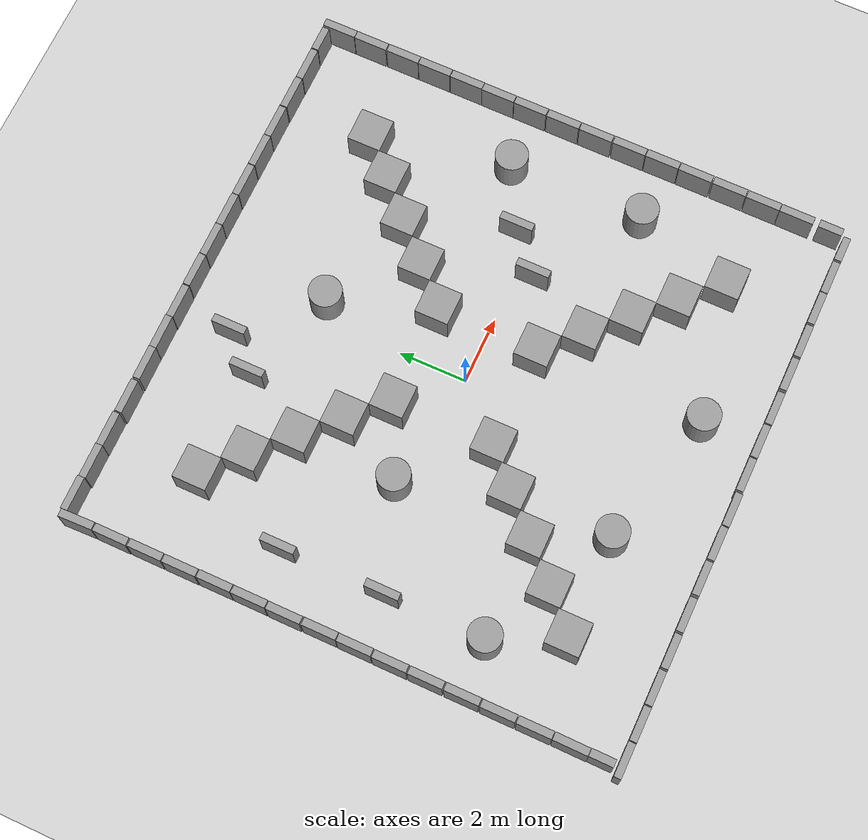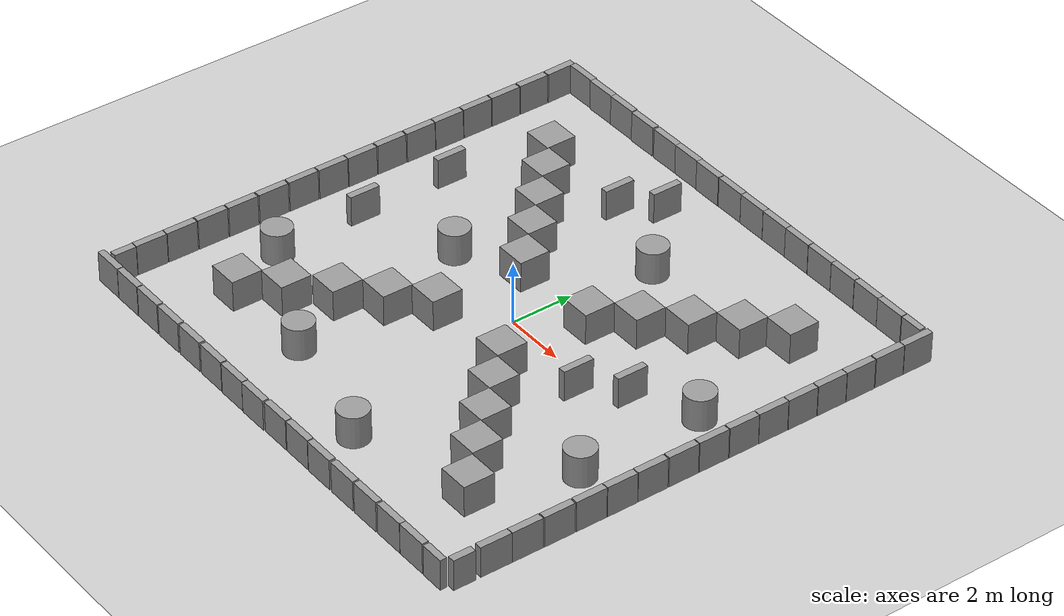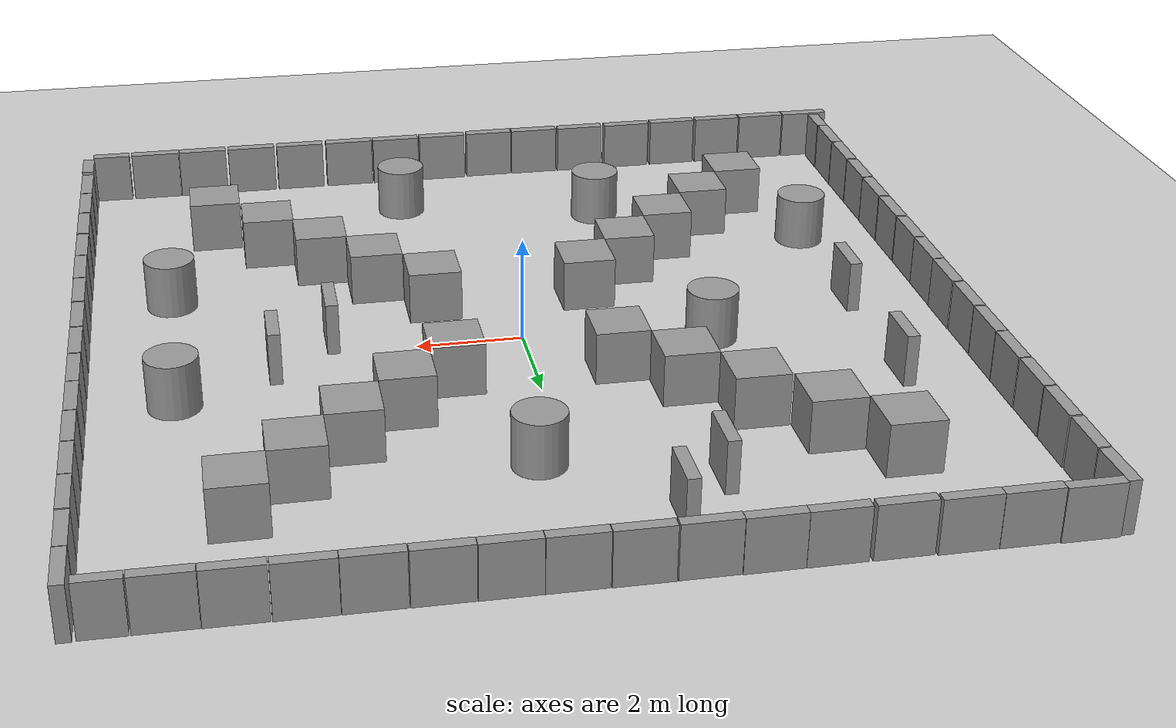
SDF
<sdf version="1.6">
 <world name="default">
  <light name="sun" type="directional">
   <pose>0 0 10 0 -0 0</pose>
   <diffuse>0.8 0.8 0.8 1</diffuse>
   <specular>0.1 0.1 0.1 1</specular>
   <attenuation>
    <range>1000</range>
    <constant>0.9</constant>
    <linear>0.01</linear>
    <quadratic>0.001</quadratic>
   </attenuation>
   <direction>-0.5 0.5 -1</direction>
  </light>
  <model name="ground_plane">
   <static>1</static>
   <static>1</static>
   <link name="link">
    <collision name="collision">
     <geometry><plane><normal>0 0 1</normal><size>100 100</size></plane></geometry>
     <surface><friction><ode><mu>100</mu><mu2>50</mu2></ode></friction></surface>
    </collision>
    <visual name="visual">
     <cast_shadows>0</cast_shadows>
     <geometry><plane><normal>0 0 1</normal><size>100 100</size></plane></geometry>
     <material>
      <script><uri>file://media/materials/scripts/gazebo.material</uri><name>Gazebo/Grey</name></script>
     </material>
    </visual>
   </link>
  </model>
  <gravity>0 0 -9.8</gravity>
  <magnetic_field>6e-06 2.3e-05 -4.2e-05</magnetic_field>
  <atmosphere type="adiabatic"/>
  <physics name="default_physics" default="0" type="ode">
   <max_step_size>0.001</max_step_size>
   <real_time_factor>1</real_time_factor>
   <real_time_update_rate>1000</real_time_update_rate>
  </physics>
  <scene><ambient>0.4 0.4 0.4 1</ambient><background>0.7 0.7 0.7 1</background><shadows>1</shadows></scene>
  <spherical_coordinates>
   <surface_model>EARTH_WGS84</surface_model>
   <latitude_deg>0</latitude_deg>
   <longitude_deg>0</longitude_deg>
   <elevation>0</elevation>
   <heading_deg>0</heading_deg>
  </spherical_coordinates>
  <audio><device>default</device></audio>
  <model name="unit_box_clone_3">
   <pose>-3.44384 8.11833 0.5 0 -0 0.009297</pose>
   <link name="link">
    <inertial>
     <mass>1</mass>
     <inertia>
      <ixx>0.166667</ixx>
      <ixy>0</ixy>
      <ixz>0</ixz>
      <iyy>0.166667</iyy>
      <iyz>0</iyz>
      <izz>0.166667</izz>
     </inertia>
    </inertial>
    <collision name="collision"><geometry><box><size>1 0.210541 1</size></box></geometry></collision>
    <visual name="visual">
     <geometry><box><size>1 0.210541 1</size></box></geometry>
     <material>
      <script><name>Gazebo/Grey</name><uri>file://media/materials/scripts/gazebo.material</uri></script>
     </material>
    </visual>
   </link>
  </model>
  <model name="unit_box_clone_4">
   <pose>-2.4437 8.12264 0.500001 0 2e-06 0.008359</pose>
   <link name="link">
    <inertial>
     <mass>1</mass>
     <inertia>
      <ixx>0.166667</ixx>
      <ixy>0</ixy>
      <ixz>0</ixz>
      <iyy>0.166667</iyy>
      <iyz>0</iyz>
      <izz>0.166667</izz>
     </inertia>
    </inertial>
    <collision name="collision"><geometry><box><size>1 0.210541 1</size></box></geometry></collision>
    <visual name="visual">
     <geometry><box><size>1 0.210541 1</size></box></geometry>
     <material>
      <script><name>Gazebo/Grey</name><uri>file://media/materials/scripts/gazebo.material</uri></script>
     </material>
    </visual>
   </link>
  </model>
  <model name="unit_box_clone_5">
   <pose>-1.4431 8.11185 0.499996 -1e-06 -9e-06 0.003021</pose>
   <link name="link">
    <inertial>
     <mass>1</mass>
     <inertia>
      <ixx>0.166667</ixx>
      <ixy>0</ixy>
      <ixz>0</ixz>
      <iyy>0.166667</iyy>
      <iyz>0</iyz>
      <izz>0.166667</izz>
     </inertia>
    </inertial>
    <collision name="collision"><geometry><box><size>1 0.210541 1</size></box></geometry></collision>
    <visual name="visual">
     <geometry><box><size>1 0.210541 1</size></box></geometry>
     <material>
      <script><name>Gazebo/Grey</name><uri>file://media/materials/scripts/gazebo.material</uri></script>
     </material>
    </visual>
   </link>
  </model>
  <model name="unit_box_clone_6">
   <pose>-0.418678 8.11842 0.5 0 -0 0.000187</pose>
   <link name="link">
    <inertial>
     <mass>1</mass>
     <inertia>
      <ixx>0.166667</ixx>
      <ixy>0</ixy>
      <ixz>0</ixz>
      <iyy>0.166667</iyy>
      <iyz>0</iyz>
      <izz>0.166667</izz>
     </inertia>
    </inertial>
    <collision name="collision"><geometry><box><size>1 0.210541 1</size></box></geometry></collision>
    <visual name="visual">
     <geometry><box><size>1 0.210541 1</size></box></geometry>
     <material>
      <script><name>Gazebo/Grey</name><uri>file://media/materials/scripts/gazebo.material</uri></script>
     </material>
    </visual>
   </link>
  </model>
  <model name="unit_box_clone_7">
   <pose>0.592841 8.11129 0.5 0 -0 0.000187</pose>
   <link name="link">
    <inertial>
     <mass>1</mass>
     <inertia>
      <ixx>0.166667</ixx>
      <ixy>0</ixy>
      <ixz>0</ixz>
      <iyy>0.166667</iyy>
      <iyz>0</iyz>
      <izz>0.166667</izz>
     </inertia>
    </inertial>
    <collision name="collision"><geometry><box><size>1 0.210541 1</size></box></geometry></collision>
    <visual name="visual">
     <geometry><box><size>1 0.210541 1</size></box></geometry>
     <material>
      <script><name>Gazebo/Grey</name><uri>file://media/materials/scripts/gazebo.material</uri></script>
     </material>
    </visual>
   </link>
  </model>
  <model name="unit_box_clone_8">
   <pose>1.60044 8.1098 0.5 0 -0 0.000187</pose>
   <link name="link">
    <inertial>
     <mass>1</mass>
     <inertia>
      <ixx>0.166667</ixx>
      <ixy>0</ixy>
      <ixz>0</ixz>
      <iyy>0.166667</iyy>
      <iyz>0</iyz>
      <izz>0.166667</izz>
     </inertia>
    </inertial>
    <collision name="collision"><geometry><box><size>1 0.210541 1</size></box></geometry></collision>
    <visual name="visual">
     <geometry><box><size>1 0.210541 1</size></box></geometry>
     <material>
      <script><name>Gazebo/Grey</name><uri>file://media/materials/scripts/gazebo.material</uri></script>
     </material>
    </visual>
   </link>
  </model>
  <model name="unit_box_clone_9">
   <pose>2.60988 8.10261 0.5 0 -0 0.000187</pose>
   <link name="link">
    <inertial>
     <mass>1</mass>
     <inertia>
      <ixx>0.166667</ixx>
      <ixy>0</ixy>
      <ixz>0</ixz>
      <iyy>0.166667</iyy>
      <iyz>0</iyz>
      <izz>0.166667</izz>
     </inertia>
    </inertial>
    <collision name="collision"><geometry><box><size>1 0.210541 1</size></box></geometry></collision>
    <visual name="visual">
     <geometry><box><size>1 0.210541 1</size></box></geometry>
     <material>
      <script><name>Gazebo/Grey</name><uri>file://media/materials/scripts/gazebo.material</uri></script>
     </material>
    </visual>
   </link>
  </model>
  <model name="unit_box_clone_10">
   <pose>3.62649 8.09902 0.5 0 -0 0.000187</pose>
   <link name="link">
    <inertial>
     <mass>1</mass>
     <inertia>
      <ixx>0.166667</ixx>
      <ixy>0</ixy>
      <ixz>0</ixz>
      <iyy>0.166667</iyy>
      <iyz>0</iyz>
      <izz>0.166667</izz>
     </inertia>
    </inertial>
    <collision name="collision"><geometry><box><size>1 0.210541 1</size></box></geometry></collision>
    <visual name="visual">
     <geometry><box><size>1 0.210541 1</size></box></geometry>
     <material>
      <script><name>Gazebo/Grey</name><uri>file://media/materials/scripts/gazebo.material</uri></script>
     </material>
    </visual>
   </link>
  </model>
  <model name="unit_box_clone_11">
   <pose>4.63311 8.09542 0.5 -0 -0 -0.003178</pose>
   <link name="link">
    <inertial>
     <mass>1</mass>
     <inertia>
      <ixx>0.166667</ixx>
      <ixy>0</ixy>
      <ixz>0</ixz>
      <iyy>0.166667</iyy>
      <iyz>0</iyz>
      <izz>0.166667</izz>
     </inertia>
    </inertial>
    <collision name="collision"><geometry><box><size>1 0.210541 1</size></box></geometry></collision>
    <visual name="visual">
     <geometry><box><size>1 0.210541 1</size></box></geometry>
     <material>
      <script><name>Gazebo/Grey</name><uri>file://media/materials/scripts/gazebo.material</uri></script>
     </material>
    </visual>
   </link>
  </model>
  <model name="unit_box_0_clone_0">
   <pose>8.11279 6.68232 0.5 0 -0 0.000127</pose>
   <link name="link">
    <inertial>
     <mass>1</mass>
     <inertia>
      <ixx>0.166667</ixx>
      <ixy>0</ixy>
      <ixz>0</ixz>
      <iyy>0.166667</iyy>
      <iyz>0</iyz>
      <izz>0.166667</izz>
     </inertia>
    </inertial>
    <collision name="collision"><geometry><box><size>0.230819 1 1</size></box></geometry></collision>
    <visual name="visual">
     <geometry><box><size>0.230819 1 1</size></box></geometry>
     <material>
      <script><name>Gazebo/Grey</name><uri>file://media/materials/scripts/gazebo.material</uri></script>
     </material>
    </visual>
   </link>
  </model>
  <model name="unit_box_0_clone_1">
   <pose>8.11915 5.6517 0.5 0 -0 0.000127</pose>
   <link name="link">
    <inertial>
     <mass>1</mass>
     <inertia>
      <ixx>0.166667</ixx>
      <ixy>0</ixy>
      <ixz>0</ixz>
      <iyy>0.166667</iyy>
      <iyz>0</iyz>
      <izz>0.166667</izz>
     </inertia>
    </inertial>
    <collision name="collision"><geometry><box><size>0.230819 1 1</size></box></geometry></collision>
    <visual name="visual">
     <geometry><box><size>0.230819 1 1</size></box></geometry>
     <material>
      <script><name>Gazebo/Grey</name><uri>file://media/materials/scripts/gazebo.material</uri></script>
     </material>
    </visual>
   </link>
  </model>
  <model name="unit_box_0_clone_2">
   <pose>8.11914 4.64017 0.5 0 -0 0.000127</pose>
   <link name="link">
    <inertial>
     <mass>1</mass>
     <inertia>
      <ixx>0.166667</ixx>
      <ixy>0</ixy>
      <ixz>0</ixz>
      <iyy>0.166667</iyy>
      <iyz>0</iyz>
      <izz>0.166667</izz>
     </inertia>
    </inertial>
    <collision name="collision"><geometry><box><size>0.230819 1 1</size></box></geometry></collision>
    <visual name="visual">
     <geometry><box><size>0.230819 1 1</size></box></geometry>
     <material>
      <script><name>Gazebo/Grey</name><uri>file://media/materials/scripts/gazebo.material</uri></script>
     </material>
    </visual>
   </link>
  </model>
  <model name="unit_box_0_clone_3">
   <pose>8.11914 3.62227 0.5 0 -0 0.000127</pose>
   <link name="link">
    <inertial>
     <mass>1</mass>
     <inertia>
      <ixx>0.166667</ixx>
      <ixy>0</ixy>
      <ixz>0</ixz>
      <iyy>0.166667</iyy>
      <iyz>0</iyz>
      <izz>0.166667</izz>
     </inertia>
    </inertial>
    <collision name="collision"><geometry><box><size>0.230819 1 1</size></box></geometry></collision>
    <visual name="visual">
     <geometry><box><size>0.230819 1 1</size></box></geometry>
     <material>
      <script><name>Gazebo/Grey</name><uri>file://media/materials/scripts/gazebo.material</uri></script>
     </material>
    </visual>
   </link>
  </model>
  <model name="unit_box_0_clone_4">
   <pose>8.11278 2.61074 0.5 0 -0 0.000127</pose>
   <link name="link">
    <inertial>
     <mass>1</mass>
     <inertia>
      <ixx>0.166667</ixx>
      <ixy>0</ixy>
      <ixz>0</ixz>
      <iyy>0.166667</iyy>
      <iyz>0</iyz>
      <izz>0.166667</izz>
     </inertia>
    </inertial>
    <collision name="collision"><geometry><box><size>0.230819 1 1</size></box></geometry></collision>
    <visual name="visual">
     <geometry><box><size>0.230819 1 1</size></box></geometry>
     <material>
      <script><name>Gazebo/Grey</name><uri>file://media/materials/scripts/gazebo.material</uri></script>
     </material>
    </visual>
   </link>
  </model>
  <model name="unit_box_0_clone_5">
   <pose>8.11277 1.5992 0.5 0 -0 0.000127</pose>
   <link name="link">
    <inertial>
     <mass>1</mass>
     <inertia>
      <ixx>0.166667</ixx>
      <ixy>0</ixy>
      <ixz>0</ixz>
      <iyy>0.166667</iyy>
      <iyz>0</iyz>
      <izz>0.166667</izz>
     </inertia>
    </inertial>
    <collision name="collision"><geometry><box><size>0.230819 1 1</size></box></geometry></collision>
    <visual name="visual">
     <geometry><box><size>0.230819 1 1</size></box></geometry>
     <material>
      <script><name>Gazebo/Grey</name><uri>file://media/materials/scripts/gazebo.material</uri></script>
     </material>
    </visual>
   </link>
  </model>
  <model name="unit_box_0_clone_6">
   <pose>8.11277 0.574943 0.5 0 -0 0.000127</pose>
   <link name="link">
    <inertial>
     <mass>1</mass>
     <inertia>
      <ixx>0.166667</ixx>
      <ixy>0</ixy>
      <ixz>0</ixz>
      <iyy>0.166667</iyy>
      <iyz>0</iyz>
      <izz>0.166667</izz>
     </inertia>
    </inertial>
    <collision name="collision"><geometry><box><size>0.230819 1 1</size></box></geometry></collision>
    <visual name="visual">
     <geometry><box><size>0.230819 1 1</size></box></geometry>
     <material>
      <script><name>Gazebo/Grey</name><uri>file://media/materials/scripts/gazebo.material</uri></script>
     </material>
    </visual>
   </link>
  </model>
  <model name="unit_box_0_clone_7">
   <pose>8.11276 -0.449315 0.5 0 -0 0.000127</pose>
   <link name="link">
    <inertial>
     <mass>1</mass>
     <inertia>
      <ixx>0.166667</ixx>
      <ixy>0</ixy>
      <ixz>0</ixz>
      <iyy>0.166667</iyy>
      <iyz>0</iyz>
      <izz>0.166667</izz>
     </inertia>
    </inertial>
    <collision name="collision"><geometry><box><size>0.230819 1 1</size></box></geometry></collision>
    <visual name="visual">
     <geometry><box><size>0.230819 1 1</size></box></geometry>
     <material>
      <script><name>Gazebo/Grey</name><uri>file://media/materials/scripts/gazebo.material</uri></script>
     </material>
    </visual>
   </link>
  </model>
  <model name="unit_box_0_clone_8">
   <pose>8.11912 -1.4863 0.5 0 -0 0.000127</pose>
   <link name="link">
    <inertial>
     <mass>1</mass>
     <inertia>
      <ixx>0.166667</ixx>
      <ixy>0</ixy>
      <ixz>0</ixz>
      <iyy>0.166667</iyy>
      <iyz>0</iyz>
      <izz>0.166667</izz>
     </inertia>
    </inertial>
    <collision name="collision"><geometry><box><size>0.230819 1 1</size></box></geometry></collision>
    <visual name="visual">
     <geometry><box><size>0.230819 1 1</size></box></geometry>
     <material>
      <script><name>Gazebo/Grey</name><uri>file://media/materials/scripts/gazebo.material</uri></script>
     </material>
    </visual>
   </link>
  </model>
  <model name="unit_box_0_clone_9">
   <pose>8.12548 -2.5042 0.5 0 -0 0.000127</pose>
   <link name="link">
    <inertial>
     <mass>1</mass>
     <inertia>
      <ixx>0.166667</ixx>
      <ixy>0</ixy>
      <ixz>0</ixz>
      <iyy>0.166667</iyy>
      <iyz>0</iyz>
      <izz>0.166667</izz>
     </inertia>
    </inertial>
    <collision name="collision"><geometry><box><size>0.230819 1 1</size></box></geometry></collision>
    <visual name="visual">
     <geometry><box><size>0.230819 1 1</size></box></geometry>
     <material>
      <script><name>Gazebo/Grey</name><uri>file://media/materials/scripts/gazebo.material</uri></script>
     </material>
    </visual>
   </link>
  </model>
  <model name="unit_box_0_clone_10">
   <pose>8.12331 -3.52222 0.5 0 -0 0.000127</pose>
   <link name="link">
    <inertial>
     <mass>1</mass>
     <inertia>
      <ixx>0.166667</ixx>
      <ixy>0</ixy>
      <ixz>0</ixz>
      <iyy>0.166667</iyy>
      <iyz>0</iyz>
      <izz>0.166667</izz>
     </inertia>
    </inertial>
    <collision name="collision"><geometry><box><size>0.230819 1 1</size></box></geometry></collision>
    <visual name="visual">
     <geometry><box><size>0.230819 1 1</size></box></geometry>
     <material>
      <script><name>Gazebo/Grey</name><uri>file://media/materials/scripts/gazebo.material</uri></script>
     </material>
    </visual>
   </link>
  </model>
  <model name="unit_box_0_clone_11">
   <pose>8.1233 -4.56315 0.5 0 -0 0.000127</pose>
   <link name="link">
    <inertial>
     <mass>1</mass>
     <inertia>
      <ixx>0.166667</ixx>
      <ixy>0</ixy>
      <ixz>0</ixz>
      <iyy>0.166667</iyy>
      <iyz>0</iyz>
      <izz>0.166667</izz>
     </inertia>
    </inertial>
    <collision name="collision"><geometry><box><size>0.230819 1 1</size></box></geometry></collision>
    <visual name="visual">
     <geometry><box><size>0.230819 1 1</size></box></geometry>
     <material>
      <script><name>Gazebo/Grey</name><uri>file://media/materials/scripts/gazebo.material</uri></script>
     </material>
    </visual>
   </link>
  </model>
  <model name="unit_box_0_clone_12">
   <pose>8.11815 -5.59377 0.5 0 -0 0.000127</pose>
   <link name="link">
    <inertial>
     <mass>1</mass>
     <inertia>
      <ixx>0.166667</ixx>
      <ixy>0</ixy>
      <ixz>0</ixz>
      <iyy>0.166667</iyy>
      <iyz>0</iyz>
      <izz>0.166667</izz>
     </inertia>
    </inertial>
    <collision name="collision"><geometry><box><size>0.230819 1 1</size></box></geometry></collision>
    <visual name="visual">
     <geometry><box><size>0.230819 1 1</size></box></geometry>
     <material>
      <script><name>Gazebo/Grey</name><uri>file://media/materials/scripts/gazebo.material</uri></script>
     </material>
    </visual>
   </link>
  </model>
  <model name="unit_box_0_clone_13">
   <pose>8.11333 -6.60776 0.5 -0 -0 -0.005608</pose>
   <link name="link">
    <inertial>
     <mass>1</mass>
     <inertia>
      <ixx>0.166667</ixx>
      <ixy>0</ixy>
      <ixz>0</ixz>
      <iyy>0.166667</iyy>
      <iyz>0</iyz>
      <izz>0.166667</izz>
     </inertia>
    </inertial>
    <collision name="collision"><geometry><box><size>0.230819 1 1</size></box></geometry></collision>
    <visual name="visual">
     <geometry><box><size>0.230819 1 1</size></box></geometry>
     <material>
      <script><name>Gazebo/Grey</name><uri>file://media/materials/scripts/gazebo.material</uri></script>
     </material>
    </visual>
   </link>
  </model>
  <model name="unit_box_clone_15_clone_0">
   <pose>6.71207 -8.1313 0.5 0 -0 0.000187</pose>
   <link name="link">
    <inertial>
     <mass>1</mass>
     <inertia>
      <ixx>0.166667</ixx>
      <ixy>0</ixy>
      <ixz>0</ixz>
      <iyy>0.166667</iyy>
      <iyz>0</iyz>
      <izz>0.166667</izz>
     </inertia>
    </inertial>
    <collision name="collision"><geometry><box><size>1 0.210541 1</size></box></geometry></collision>
    <visual name="visual">
     <geometry><box><size>1 0.210541 1</size></box></geometry>
     <material>
      <script><name>Gazebo/Grey</name><uri>file://media/materials/scripts/gazebo.material</uri></script>
     </material>
    </visual>
   </link>
  </model>
  <model name="unit_box_clone_15_clone_1">
   <pose>5.69716 -8.13129 0.5 0 -0 0.000187</pose>
   <link name="link">
    <inertial>
     <mass>1</mass>
     <inertia>
      <ixx>0.166667</ixx>
      <ixy>0</ixy>
      <ixz>0</ixz>
      <iyy>0.166667</iyy>
      <iyz>0</iyz>
      <izz>0.166667</izz>
     </inertia>
    </inertial>
    <collision name="collision"><geometry><box><size>1 0.210541 1</size></box></geometry></collision>
    <visual name="visual">
     <geometry><box><size>1 0.210541 1</size></box></geometry>
     <material>
      <script><name>Gazebo/Grey</name><uri>file://media/materials/scripts/gazebo.material</uri></script>
     </material>
    </visual>
   </link>
  </model>
  <model name="unit_box_clone_15_clone_2">
   <pose>4.63882 -8.13747 0.5 0 -0 0.000187</pose>
   <link name="link">
    <inertial>
     <mass>1</mass>
     <inertia>
      <ixx>0.166667</ixx>
      <ixy>0</ixy>
      <ixz>0</ixz>
      <iyy>0.166667</iyy>
      <iyz>0</iyz>
      <izz>0.166667</izz>
     </inertia>
    </inertial>
    <collision name="collision"><geometry><box><size>1 0.210541 1</size></box></geometry></collision>
    <visual name="visual">
     <geometry><box><size>1 0.210541 1</size></box></geometry>
     <material>
      <script><name>Gazebo/Grey</name><uri>file://media/materials/scripts/gazebo.material</uri></script>
     </material>
    </visual>
   </link>
  </model>
  <model name="unit_box_clone_15_clone_3">
   <pose>3.57976 -8.13747 0.5 0 -0 0.000187</pose>
   <link name="link">
    <inertial>
     <mass>1</mass>
     <inertia>
      <ixx>0.166667</ixx>
      <ixy>0</ixy>
      <ixz>0</ixz>
      <iyy>0.166667</iyy>
      <iyz>0</iyz>
      <izz>0.166667</izz>
     </inertia>
    </inertial>
    <collision name="collision"><geometry><box><size>1 0.210541 1</size></box></geometry></collision>
    <visual name="visual">
     <geometry><box><size>1 0.210541 1</size></box></geometry>
     <material>
      <script><name>Gazebo/Grey</name><uri>file://media/materials/scripts/gazebo.material</uri></script>
     </material>
    </visual>
   </link>
  </model>
  <model name="unit_box_clone_15_clone_4">
   <pose>2.49816 -8.13746 0.5 0 -0 0.000187</pose>
   <link name="link">
    <inertial>
     <mass>1</mass>
     <inertia>
      <ixx>0.166667</ixx>
      <ixy>0</ixy>
      <ixz>0</ixz>
      <iyy>0.166667</iyy>
      <iyz>0</iyz>
      <izz>0.166667</izz>
     </inertia>
    </inertial>
    <collision name="collision"><geometry><box><size>1 0.210541 1</size></box></geometry></collision>
    <visual name="visual">
     <geometry><box><size>1 0.210541 1</size></box></geometry>
     <material>
      <script><name>Gazebo/Grey</name><uri>file://media/materials/scripts/gazebo.material</uri></script>
     </material>
    </visual>
   </link>
  </model>
  <model name="unit_box_clone_15_clone_5">
   <pose>1.46162 -8.12619 0.5 0 -0 0.000187</pose>
   <link name="link">
    <inertial>
     <mass>1</mass>
     <inertia>
      <ixx>0.166667</ixx>
      <ixy>0</ixy>
      <ixz>0</ixz>
      <iyy>0.166667</iyy>
      <iyz>0</iyz>
      <izz>0.166667</izz>
     </inertia>
    </inertial>
    <collision name="collision"><geometry><box><size>1 0.210541 1</size></box></geometry></collision>
    <visual name="visual">
     <geometry><box><size>1 0.210541 1</size></box></geometry>
     <material>
      <script><name>Gazebo/Grey</name><uri>file://media/materials/scripts/gazebo.material</uri></script>
     </material>
    </visual>
   </link>
  </model>
  <model name="unit_box_clone_15_clone_6">
   <pose>0.425094 -8.12618 0.5 0 -0 0.000187</pose>
   <link name="link">
    <inertial>
     <mass>1</mass>
     <inertia>
      <ixx>0.166667</ixx>
      <ixy>0</ixy>
      <ixz>0</ixz>
      <iyy>0.166667</iyy>
      <iyz>0</iyz>
      <izz>0.166667</izz>
     </inertia>
    </inertial>
    <collision name="collision"><geometry><box><size>1 0.210541 1</size></box></geometry></collision>
    <visual name="visual">
     <geometry><box><size>1 0.210541 1</size></box></geometry>
     <material>
      <script><name>Gazebo/Grey</name><uri>file://media/materials/scripts/gazebo.material</uri></script>
     </material>
    </visual>
   </link>
  </model>
  <model name="unit_box_clone_15_clone_7">
   <pose>-0.633968 -8.14873 0.5 0 -0 0.000187</pose>
   <link name="link">
    <inertial>
     <mass>1</mass>
     <inertia>
      <ixx>0.166667</ixx>
      <ixy>0</ixy>
      <ixz>0</ixz>
      <iyy>0.166667</iyy>
      <iyz>0</iyz>
      <izz>0.166667</izz>
     </inertia>
    </inertial>
    <collision name="collision"><geometry><box><size>1 0.210541 1</size></box></geometry></collision>
    <visual name="visual">
     <geometry><box><size>1 0.210541 1</size></box></geometry>
     <material>
      <script><name>Gazebo/Grey</name><uri>file://media/materials/scripts/gazebo.material</uri></script>
     </material>
    </visual>
   </link>
  </model>
  <model name="unit_box_clone_15_clone_8">
   <pose>-1.65922 -8.13745 0.5 0 -0 0.000187</pose>
   <link name="link">
    <inertial>
     <mass>1</mass>
     <inertia>
      <ixx>0.166667</ixx>
      <ixy>0</ixy>
      <ixz>0</ixz>
      <iyy>0.166667</iyy>
      <iyz>0</iyz>
      <izz>0.166667</izz>
     </inertia>
    </inertial>
    <collision name="collision"><geometry><box><size>1 0.210541 1</size></box></geometry></collision>
    <visual name="visual">
     <geometry><box><size>1 0.210541 1</size></box></geometry>
     <material>
      <script><name>Gazebo/Grey</name><uri>file://media/materials/scripts/gazebo.material</uri></script>
     </material>
    </visual>
   </link>
  </model>
  <model name="unit_box_clone_15_clone_9">
   <pose>-2.70702 -8.1262 0.5 0 -0 0.000187</pose>
   <link name="link">
    <inertial>
     <mass>1</mass>
     <inertia>
      <ixx>0.166667</ixx>
      <ixy>0</ixy>
      <ixz>0</ixz>
      <iyy>0.166667</iyy>
      <iyz>0</iyz>
      <izz>0.166667</izz>
     </inertia>
    </inertial>
    <collision name="collision"><geometry><box><size>1 0.210541 1</size></box></geometry></collision>
    <visual name="visual">
     <geometry><box><size>1 0.210541 1</size></box></geometry>
     <material>
      <script><name>Gazebo/Grey</name><uri>file://media/materials/scripts/gazebo.material</uri></script>
     </material>
    </visual>
   </link>
  </model>
  <model name="unit_box_0_clone_4_clone">
   <pose>-8.14591 7.71693 0.499549 0 -0 0.031457</pose>
   <link name="link">
    <inertial>
     <mass>1</mass>
     <inertia>
      <ixx>0.166667</ixx>
      <ixy>0</ixy>
      <ixz>0</ixz>
      <iyy>0.166667</iyy>
      <iyz>0</iyz>
      <izz>0.166667</izz>
     </inertia>
    </inertial>
    <collision name="collision"><geometry><box><size>0.230819 1 1</size></box></geometry></collision>
    <visual name="visual">
     <geometry><box><size>0.230819 1 1</size></box></geometry>
     <material>
      <script><name>Gazebo/Grey</name><uri>file://media/materials/scripts/gazebo.material</uri></script>
     </material>
    </visual>
   </link>
  </model>
  <model name="unit_box_0_clone_4_clone_0">
   <pose>-8.13281 6.68715 0.5 0 -0 0.000127</pose>
   <link name="link">
    <inertial>
     <mass>1</mass>
     <inertia>
      <ixx>0.166667</ixx>
      <ixy>0</ixy>
      <ixz>0</ixz>
      <iyy>0.166667</iyy>
      <iyz>0</iyz>
      <izz>0.166667</izz>
     </inertia>
    </inertial>
    <collision name="collision"><geometry><box><size>0.230819 1 1</size></box></geometry></collision>
    <visual name="visual">
     <geometry><box><size>0.230819 1 1</size></box></geometry>
     <material>
      <script><name>Gazebo/Grey</name><uri>file://media/materials/scripts/gazebo.material</uri></script>
     </material>
    </visual>
   </link>
  </model>
  <model name="unit_box_0_clone_4_clone_1">
   <pose>-8.12606 5.64723 0.5 0 -0 0.000127</pose>
   <link name="link">
    <inertial>
     <mass>1</mass>
     <inertia>
      <ixx>0.166667</ixx>
      <ixy>0</ixy>
      <ixz>0</ixz>
      <iyy>0.166667</iyy>
      <iyz>0</iyz>
      <izz>0.166667</izz>
     </inertia>
    </inertial>
    <collision name="collision"><geometry><box><size>0.230819 1 1</size></box></geometry></collision>
    <visual name="visual">
     <geometry><box><size>0.230819 1 1</size></box></geometry>
     <material>
      <script><name>Gazebo/Grey</name><uri>file://media/materials/scripts/gazebo.material</uri></script>
     </material>
    </visual>
   </link>
  </model>
  <model name="unit_box_0_clone_4_clone_2">
   <pose>-8.12607 4.62081 0.5 0 -0 0.000127</pose>
   <link name="link">
    <inertial>
     <mass>1</mass>
     <inertia>
      <ixx>0.166667</ixx>
      <ixy>0</ixy>
      <ixz>0</ixz>
      <iyy>0.166667</iyy>
      <iyz>0</iyz>
      <izz>0.166667</izz>
     </inertia>
    </inertial>
    <collision name="collision"><geometry><box><size>0.230819 1 1</size></box></geometry></collision>
    <visual name="visual">
     <geometry><box><size>0.230819 1 1</size></box></geometry>
     <material>
      <script><name>Gazebo/Grey</name><uri>file://media/materials/scripts/gazebo.material</uri></script>
     </material>
    </visual>
   </link>
  </model>
  <model name="unit_box_0_clone_4_clone_3">
   <pose>-8.11932 3.59439 0.5 0 -0 0.000127</pose>
   <link name="link">
    <inertial>
     <mass>1</mass>
     <inertia>
      <ixx>0.166667</ixx>
      <ixy>0</ixy>
      <ixz>0</ixz>
      <iyy>0.166667</iyy>
      <iyz>0</iyz>
      <izz>0.166667</izz>
     </inertia>
    </inertial>
    <collision name="collision"><geometry><box><size>0.230819 1 1</size></box></geometry></collision>
    <visual name="visual">
     <geometry><box><size>0.230819 1 1</size></box></geometry>
     <material>
      <script><name>Gazebo/Grey</name><uri>file://media/materials/scripts/gazebo.material</uri></script>
     </material>
    </visual>
   </link>
  </model>
  <model name="unit_box_0_clone_4_clone_4">
   <pose>-8.11932 2.57473 0.5 0 -0 0.000127</pose>
   <link name="link">
    <inertial>
     <mass>1</mass>
     <inertia>
      <ixx>0.166667</ixx>
      <ixy>0</ixy>
      <ixz>0</ixz>
      <iyy>0.166667</iyy>
      <iyz>0</iyz>
      <izz>0.166667</izz>
     </inertia>
    </inertial>
    <collision name="collision"><geometry><box><size>0.230819 1 1</size></box></geometry></collision>
    <visual name="visual">
     <geometry><box><size>0.230819 1 1</size></box></geometry>
     <material>
      <script><name>Gazebo/Grey</name><uri>file://media/materials/scripts/gazebo.material</uri></script>
     </material>
    </visual>
   </link>
  </model>
  <model name="unit_box_0_clone_4_clone_5">
   <pose>-8.12608 1.54156 0.5 0 -0 0.000127</pose>
   <link name="link">
    <inertial>
     <mass>1</mass>
     <inertia>
      <ixx>0.166667</ixx>
      <ixy>0</ixy>
      <ixz>0</ixz>
      <iyy>0.166667</iyy>
      <iyz>0</iyz>
      <izz>0.166667</izz>
     </inertia>
    </inertial>
    <collision name="collision"><geometry><box><size>0.230819 1 1</size></box></geometry></collision>
    <visual name="visual">
     <geometry><box><size>0.230819 1 1</size></box></geometry>
     <material>
      <script><name>Gazebo/Grey</name><uri>file://media/materials/scripts/gazebo.material</uri></script>
     </material>
    </visual>
   </link>
  </model>
  <model name="unit_box_0_clone_4_clone_6">
   <pose>-8.11933 0.501635 0.5 0 -0 0.000127</pose>
   <link name="link">
    <inertial>
     <mass>1</mass>
     <inertia>
      <ixx>0.166667</ixx>
      <ixy>0</ixy>
      <ixz>0</ixz>
      <iyy>0.166667</iyy>
      <iyz>0</iyz>
      <izz>0.166667</izz>
     </inertia>
    </inertial>
    <collision name="collision"><geometry><box><size>0.230819 1 1</size></box></geometry></collision>
    <visual name="visual">
     <geometry><box><size>0.230819 1 1</size></box></geometry>
     <material>
      <script><name>Gazebo/Grey</name><uri>file://media/materials/scripts/gazebo.material</uri></script>
     </material>
    </visual>
   </link>
  </model>
  <model name="unit_box_0_clone_4_clone_7">
   <pose>-8.12609 -0.518029 0.5 0 -0 0.000127</pose>
   <link name="link">
    <inertial>
     <mass>1</mass>
     <inertia>
      <ixx>0.166667</ixx>
      <ixy>0</ixy>
      <ixz>0</ixz>
      <iyy>0.166667</iyy>
      <iyz>0</iyz>
      <izz>0.166667</izz>
     </inertia>
    </inertial>
    <collision name="collision"><geometry><box><size>0.230819 1 1</size></box></geometry></collision>
    <visual name="visual">
     <geometry><box><size>0.230819 1 1</size></box></geometry>
     <material>
      <script><name>Gazebo/Grey</name><uri>file://media/materials/scripts/gazebo.material</uri></script>
     </material>
    </visual>
   </link>
  </model>
  <model name="unit_box_0_clone_4_clone_8">
   <pose>-8.13284 -1.54445 0.5 0 -0 0.000127</pose>
   <link name="link">
    <inertial>
     <mass>1</mass>
     <inertia>
      <ixx>0.166667</ixx>
      <ixy>0</ixy>
      <ixz>0</ixz>
      <iyy>0.166667</iyy>
      <iyz>0</iyz>
      <izz>0.166667</izz>
     </inertia>
    </inertial>
    <collision name="collision"><geometry><box><size>0.230819 1 1</size></box></geometry></collision>
    <visual name="visual">
     <geometry><box><size>0.230819 1 1</size></box></geometry>
     <material>
      <script><name>Gazebo/Grey</name><uri>file://media/materials/scripts/gazebo.material</uri></script>
     </material>
    </visual>
   </link>
  </model>
  <model name="unit_box_0_clone_4_clone_9">
   <pose>-8.13285 -2.58437 0.5 0 -0 0.000127</pose>
   <link name="link">
    <inertial>
     <mass>1</mass>
     <inertia>
      <ixx>0.166667</ixx>
      <ixy>0</ixy>
      <ixz>0</ixz>
      <iyy>0.166667</iyy>
      <iyz>0</iyz>
      <izz>0.166667</izz>
     </inertia>
    </inertial>
    <collision name="collision"><geometry><box><size>0.230819 1 1</size></box></geometry></collision>
    <visual name="visual">
     <geometry><box><size>0.230819 1 1</size></box></geometry>
     <material>
      <script><name>Gazebo/Grey</name><uri>file://media/materials/scripts/gazebo.material</uri></script>
     </material>
    </visual>
   </link>
  </model>
  <model name="unit_box_0_clone_4_clone_10">
   <pose>-8.13285 -3.62429 0.5 0 -0 0.000127</pose>
   <link name="link">
    <inertial>
     <mass>1</mass>
     <inertia>
      <ixx>0.166667</ixx>
      <ixy>0</ixy>
      <ixz>0</ixz>
      <iyy>0.166667</iyy>
      <iyz>0</iyz>
      <izz>0.166667</izz>
     </inertia>
    </inertial>
    <collision name="collision"><geometry><box><size>0.230819 1 1</size></box></geometry></collision>
    <visual name="visual">
     <geometry><box><size>0.230819 1 1</size></box></geometry>
     <material>
      <script><name>Gazebo/Grey</name><uri>file://media/materials/scripts/gazebo.material</uri></script>
     </material>
    </visual>
   </link>
  </model>
  <model name="unit_box_0_clone_4_clone_11">
   <pose>-8.1396 -4.65746 0.5 0 -0 0.000127</pose>
   <link name="link">
    <inertial>
     <mass>1</mass>
     <inertia>
      <ixx>0.166667</ixx>
      <ixy>0</ixy>
      <ixz>0</ixz>
      <iyy>0.166667</iyy>
      <iyz>0</iyz>
      <izz>0.166667</izz>
     </inertia>
    </inertial>
    <collision name="collision"><geometry><box><size>0.230819 1 1</size></box></geometry></collision>
    <visual name="visual">
     <geometry><box><size>0.230819 1 1</size></box></geometry>
     <material>
      <script><name>Gazebo/Grey</name><uri>file://media/materials/scripts/gazebo.material</uri></script>
     </material>
    </visual>
   </link>
  </model>
  <model name="unit_box_0_clone_4_clone_12">
   <pose>-8.1396 -5.69063 0.5 0 -0 0.000127</pose>
   <link name="link">
    <inertial>
     <mass>1</mass>
     <inertia>
      <ixx>0.166667</ixx>
      <ixy>0</ixy>
      <ixz>0</ixz>
      <iyy>0.166667</iyy>
      <iyz>0</iyz>
      <izz>0.166667</izz>
     </inertia>
    </inertial>
    <collision name="collision"><geometry><box><size>0.230819 1 1</size></box></geometry></collision>
    <visual name="visual">
     <geometry><box><size>0.230819 1 1</size></box></geometry>
     <material>
      <script><name>Gazebo/Grey</name><uri>file://media/materials/scripts/gazebo.material</uri></script>
     </material>
    </visual>
   </link>
  </model>
  <model name="unit_box_0_clone_4_clone_13">
   <pose>-8.14113 -6.70872 0.5 1e-06 -1e-06 -0.009587</pose>
   <link name="link">
    <inertial>
     <mass>1</mass>
     <inertia>
      <ixx>0.166667</ixx>
      <ixy>0</ixy>
      <ixz>0</ixz>
      <iyy>0.166667</iyy>
      <iyz>0</iyz>
      <izz>0.166667</izz>
     </inertia>
    </inertial>
    <collision name="collision"><geometry><box><size>0.230819 1 1</size></box></geometry></collision>
    <visual name="visual">
     <geometry><box><size>0.230819 1 1</size></box></geometry>
     <material>
      <script><name>Gazebo/Grey</name><uri>file://media/materials/scripts/gazebo.material</uri></script>
     </material>
    </visual>
   </link>
  </model>
  <model name="unit_box_0_clone_0_clone">
   <pose>8.11438 7.69322 0.5 0 -0 0.000167</pose>
   <link name="link">
    <inertial>
     <mass>1</mass>
     <inertia>
      <ixx>0.166667</ixx>
      <ixy>0</ixy>
      <ixz>0</ixz>
      <iyy>0.166667</iyy>
      <iyz>0</iyz>
      <izz>0.166667</izz>
     </inertia>
    </inertial>
    <collision name="collision"><geometry><box><size>0.230819 1 1</size></box></geometry></collision>
    <visual name="visual">
     <geometry><box><size>0.230819 1 1</size></box></geometry>
     <material>
      <script><name>Gazebo/Grey</name><uri>file://media/materials/scripts/gazebo.material</uri></script>
     </material>
    </visual>
   </link>
  </model>
  <model name="unit_box_clone_11_clone">
   <pose>5.65439 8.08332 0.5 -0 -0 -0.003121</pose>
   <link name="link">
    <inertial>
     <mass>1</mass>
     <inertia>
      <ixx>0.166667</ixx>
      <ixy>0</ixy>
      <ixz>0</ixz>
      <iyy>0.166667</iyy>
      <iyz>0</iyz>
      <izz>0.166667</izz>
     </inertia>
    </inertial>
    <collision name="collision"><geometry><box><size>1 0.210541 1</size></box></geometry></collision>
    <visual name="visual">
     <geometry><box><size>1 0.210541 1</size></box></geometry>
     <material>
      <script><name>Gazebo/Grey</name><uri>file://media/materials/scripts/gazebo.material</uri></script>
     </material>
    </visual>
   </link>
  </model>
  <model name="unit_box_clone_11_clone_0">
   <pose>6.66439 8.07321 0.5 0 0 -0.003043</pose>
   <link name="link">
    <inertial>
     <mass>1</mass>
     <inertia>
      <ixx>0.166667</ixx>
      <ixy>0</ixy>
      <ixz>0</ixz>
      <iyy>0.166667</iyy>
      <iyz>0</iyz>
      <izz>0.166667</izz>
     </inertia>
    </inertial>
    <collision name="collision"><geometry><box><size>1 0.210541 1</size></box></geometry></collision>
    <visual name="visual">
     <geometry><box><size>1 0.210541 1</size></box></geometry>
     <material>
      <script><name>Gazebo/Grey</name><uri>file://media/materials/scripts/gazebo.material</uri></script>
     </material>
    </visual>
   </link>
  </model>
  <model name="unit_box_clone_11_clone_1_clone">
   <pose>7.56437 8.07323 0.499997 2e-06 -7e-06 -0.003734</pose>
   <link name="link">
    <inertial>
     <mass>1</mass>
     <inertia>
      <ixx>0.166667</ixx>
      <ixy>0</ixy>
      <ixz>0</ixz>
      <iyy>0.166667</iyy>
      <iyz>0</iyz>
      <izz>0.166667</izz>
     </inertia>
    </inertial>
    <collision name="collision"><geometry><box><size>0.750223 0.210541 1</size></box></geometry></collision>
    <visual name="visual">
     <geometry><box><size>0.750223 0.210541 1</size></box></geometry>
     <material>
      <script><name>Gazebo/Grey</name><uri>file://media/materials/scripts/gazebo.material</uri></script>
     </material>
    </visual>
   </link>
  </model>
  <model name="unit_box_0_clone_4_clone_13_clone_clone">
   <pose>-8.13833 -7.57659 0.500001 1e-06 -0 -0.007573</pose>
   <link name="link">
    <inertial>
     <mass>1</mass>
     <inertia>
      <ixx>0.166667</ixx>
      <ixy>0</ixy>
      <ixz>0</ixz>
      <iyy>0.166667</iyy>
      <iyz>0</iyz>
      <izz>0.166667</izz>
     </inertia>
    </inertial>
    <collision name="collision"><geometry><box><size>0.230819 0.700336 1</size></box></geometry></collision>
    <visual name="visual">
     <geometry><box><size>0.230819 0.700336 1</size></box></geometry>
     <material>
      <script><name>Gazebo/Grey</name><uri>file://media/materials/scripts/gazebo.material</uri></script>
     </material>
    </visual>
   </link>
  </model>
  <model name="unit_box_clone_11_clone_1_clone_2">
   <pose>7.64249 -8.13927 0.499997 -2e-06 8e-06 -0.005754</pose>
   <link name="link">
    <inertial>
     <mass>1</mass>
     <inertia>
      <ixx>0.166667</ixx>
      <ixy>0</ixy>
      <ixz>0</ixz>
      <iyy>0.166667</iyy>
      <iyz>0</iyz>
      <izz>0.166667</izz>
     </inertia>
    </inertial>
    <collision name="collision"><geometry><box><size>0.750223 0.210541 1</size></box></geometry></collision>
    <visual name="visual">
     <geometry><box><size>0.750223 0.210541 1</size></box></geometry>
     <material>
      <script><name>Gazebo/Grey</name><uri>file://media/materials/scripts/gazebo.material</uri></script>
     </material>
    </visual>
   </link>
  </model>
  <model name="unit_box_0_clone_4_clone_13_clone_clone_clone">
   <pose>8.11858 -7.62155 0.499997 -7e-06 -3e-06 -0.005341</pose>
   <link name="link">
    <inertial>
     <mass>1</mass>
     <inertia>
      <ixx>0.166667</ixx>
      <ixy>0</ixy>
      <ixz>0</ixz>
      <iyy>0.166667</iyy>
      <iyz>0</iyz>
      <izz>0.166667</izz>
     </inertia>
    </inertial>
    <collision name="collision"><geometry><box><size>0.230819 0.700336 1</size></box></geometry></collision>
    <visual name="visual">
     <geometry><box><size>0.230819 0.700336 1</size></box></geometry>
     <material>
      <script><name>Gazebo/Grey</name><uri>file://media/materials/scripts/gazebo.material</uri></script>
     </material>
    </visual>
   </link>
  </model>
  <model name="unit_box_clone_12">
   <pose>-4.50592 4.49343 0.499995 0 1e-05 2e-06</pose>
   <link name="link">
    <inertial>
     <mass>1</mass>
     <inertia>
      <ixx>0.166667</ixx>
      <ixy>0</ixy>
      <ixz>0</ixz>
      <iyy>0.166667</iyy>
      <iyz>0</iyz>
      <izz>0.166667</izz>
     </inertia>
    </inertial>
    <collision name="collision"><geometry><box><size>1 1 1</size></box></geometry></collision>
    <visual name="visual">
     <geometry><box><size>1 1 1</size></box></geometry>
     <material>
      <script><name>Gazebo/Grey</name><uri>file://media/materials/scripts/gazebo.material</uri></script>
     </material>
    </visual>
   </link>
  </model>
  <model name="unit_box_clone_15">
   <pose>-1.48348 1.49238 0.499995 1e-05 -0 2e-06</pose>
   <link name="link">
    <inertial>
     <mass>1</mass>
     <inertia>
      <ixx>0.166667</ixx>
      <ixy>0</ixy>
      <ixz>0</ixz>
      <iyy>0.166667</iyy>
      <iyz>0</iyz>
      <izz>0.166667</izz>
     </inertia>
    </inertial>
    <collision name="collision"><geometry><box><size>1 1 1</size></box></geometry></collision>
    <visual name="visual">
     <geometry><box><size>1 1 1</size></box></geometry>
     <material>
      <script><name>Gazebo/Grey</name><uri>file://media/materials/scripts/gazebo.material</uri></script>
     </material>
    </visual>
   </link>
  </model>
  <model name="unit_box_clone_14">
   <pose>-2.47914 2.49785 0.499995 -1e-05 0 0.000563</pose>
   <link name="link">
    <inertial>
     <mass>1</mass>
     <inertia>
      <ixx>0.166667</ixx>
      <ixy>0</ixy>
      <ixz>0</ixz>
      <iyy>0.166667</iyy>
      <iyz>0</iyz>
      <izz>0.166667</izz>
     </inertia>
    </inertial>
    <collision name="collision"><geometry><box><size>1 1 1</size></box></geometry></collision>
    <visual name="visual">
     <geometry><box><size>1 1 1</size></box></geometry>
     <material>
      <script><name>Gazebo/Grey</name><uri>file://media/materials/scripts/gazebo.material</uri></script>
     </material>
    </visual>
   </link>
  </model>
  <model name="unit_box_clone_13">
   <pose>-3.47823 3.4973 0.499995 1e-05 -0 0.000526</pose>
   <link name="link">
    <inertial>
     <mass>1</mass>
     <inertia>
      <ixx>0.166667</ixx>
      <ixy>0</ixy>
      <ixz>0</ixz>
      <iyy>0.166667</iyy>
      <iyz>0</iyz>
      <izz>0.166667</izz>
     </inertia>
    </inertial>
    <collision name="collision"><geometry><box><size>1 1 1</size></box></geometry></collision>
    <visual name="visual">
     <geometry><box><size>1 1 1</size></box></geometry>
     <material>
      <script><name>Gazebo/Grey</name><uri>file://media/materials/scripts/gazebo.material</uri></script>
     </material>
    </visual>
   </link>
  </model>
  <model name="unit_box_clone_16">
   <pose>1.5007 -1.49592 0.499995 0 1e-05 2e-06</pose>
   <link name="link">
    <inertial>
     <mass>1</mass>
     <inertia>
      <ixx>0.166667</ixx>
      <ixy>0</ixy>
      <ixz>0</ixz>
      <iyy>0.166667</iyy>
      <iyz>0</iyz>
      <izz>0.166667</izz>
     </inertia>
    </inertial>
    <collision name="collision"><geometry><box><size>1 1 1</size></box></geometry></collision>
    <visual name="visual">
     <geometry><box><size>1 1 1</size></box></geometry>
     <material>
      <script><name>Gazebo/Grey</name><uri>file://media/materials/scripts/gazebo.material</uri></script>
     </material>
    </visual>
   </link>
  </model>
  <model name="unit_box_clone_17">
   <pose>2.51298 -2.50799 0.499995 0 -1e-05 0.000614</pose>
   <link name="link">
    <inertial>
     <mass>1</mass>
     <inertia>
      <ixx>0.166667</ixx>
      <ixy>0</ixy>
      <ixz>0</ixz>
      <iyy>0.166667</iyy>
      <iyz>0</iyz>
      <izz>0.166667</izz>
     </inertia>
    </inertial>
    <collision name="collision"><geometry><box><size>1 1 1</size></box></geometry></collision>
    <visual name="visual">
     <geometry><box><size>1 1 1</size></box></geometry>
     <material>
      <script><name>Gazebo/Grey</name><uri>file://media/materials/scripts/gazebo.material</uri></script>
     </material>
    </visual>
   </link>
  </model>
  <model name="unit_box_clone_18">
   <pose>3.49779 -3.5071 0.499995 0 1e-05 0.00122</pose>
   <link name="link">
    <inertial>
     <mass>1</mass>
     <inertia>
      <ixx>0.166667</ixx>
      <ixy>0</ixy>
      <ixz>0</ixz>
      <iyy>0.166667</iyy>
      <iyz>0</iyz>
      <izz>0.166667</izz>
     </inertia>
    </inertial>
    <collision name="collision"><geometry><box><size>1 1 1</size></box></geometry></collision>
    <visual name="visual">
     <geometry><box><size>1 1 1</size></box></geometry>
     <material>
      <script><name>Gazebo/Grey</name><uri>file://media/materials/scripts/gazebo.material</uri></script>
     </material>
    </visual>
   </link>
  </model>
  <model name="unit_box_clone_19">
   <pose>4.4826 -4.50619 0.499995 0 1e-05 0.00065</pose>
   <link name="link">
    <inertial>
     <mass>1</mass>
     <inertia>
      <ixx>0.166667</ixx>
      <ixy>0</ixy>
      <ixz>0</ixz>
      <iyy>0.166667</iyy>
      <iyz>0</iyz>
      <izz>0.166667</izz>
     </inertia>
    </inertial>
    <collision name="collision"><geometry><box><size>1 1 1</size></box></geometry></collision>
    <visual name="visual">
     <geometry><box><size>1 1 1</size></box></geometry>
     <material>
      <script><name>Gazebo/Grey</name><uri>file://media/materials/scripts/gazebo.material</uri></script>
     </material>
    </visual>
   </link>
  </model>
  <model name="unit_box_clone_20">
   <pose>5.50895 -5.53233 0.499995 0 1e-05 2e-06</pose>
   <link name="link">
    <inertial>
     <mass>1</mass>
     <inertia>
      <ixx>0.166667</ixx>
      <ixy>0</ixy>
      <ixz>0</ixz>
      <iyy>0.166667</iyy>
      <iyz>0</iyz>
      <izz>0.166667</izz>
     </inertia>
    </inertial>
    <collision name="collision"><geometry><box><size>1 1 1</size></box></geometry></collision>
    <visual name="visual">
     <geometry><box><size>1 1 1</size></box></geometry>
     <material>
      <script><name>Gazebo/Grey</name><uri>file://media/materials/scripts/gazebo.material</uri></script>
     </material>
    </visual>
   </link>
  </model>
  <model name="unit_box_clone_21">
   <pose>1.50378 1.50084 0.499995 0 1e-05 0.00104</pose>
   <link name="link">
    <inertial>
     <mass>1</mass>
     <inertia>
      <ixx>0.166667</ixx>
      <ixy>0</ixy>
      <ixz>0</ixz>
      <iyy>0.166667</iyy>
      <iyz>0</iyz>
      <izz>0.166667</izz>
     </inertia>
    </inertial>
    <collision name="collision"><geometry><box><size>1 1 1</size></box></geometry></collision>
    <visual name="visual">
     <geometry><box><size>1 1 1</size></box></geometry>
     <material>
      <script><name>Gazebo/Grey</name><uri>file://media/materials/scripts/gazebo.material</uri></script>
     </material>
    </visual>
   </link>
  </model>
  <model name="unit_box_clone_22">
   <pose>2.5028 2.49916 0.499995 0 1e-05 0.000941</pose>
   <link name="link">
    <inertial>
     <mass>1</mass>
     <inertia>
      <ixx>0.166667</ixx>
      <ixy>0</ixy>
      <ixz>0</ixz>
      <iyy>0.166667</iyy>
      <iyz>0</iyz>
      <izz>0.166667</izz>
     </inertia>
    </inertial>
    <collision name="collision"><geometry><box><size>1 1 1</size></box></geometry></collision>
    <visual name="visual">
     <geometry><box><size>1 1 1</size></box></geometry>
     <material>
      <script><name>Gazebo/Grey</name><uri>file://media/materials/scripts/gazebo.material</uri></script>
     </material>
    </visual>
   </link>
  </model>
  <model name="unit_box_clone_23">
   <pose>3.51093 3.50762 0.499995 0 1e-05 2e-06</pose>
   <link name="link">
    <inertial>
     <mass>1</mass>
     <inertia>
      <ixx>0.166667</ixx>
      <ixy>0</ixy>
      <ixz>0</ixz>
      <iyy>0.166667</iyy>
      <iyz>0</iyz>
      <izz>0.166667</izz>
     </inertia>
    </inertial>
    <collision name="collision"><geometry><box><size>1 1 1</size></box></geometry></collision>
    <visual name="visual">
     <geometry><box><size>1 1 1</size></box></geometry>
     <material>
      <script><name>Gazebo/Grey</name><uri>file://media/materials/scripts/gazebo.material</uri></script>
     </material>
    </visual>
   </link>
  </model>
  <model name="unit_box_clone_24">
   <pose>4.51534 4.5023 0.499995 0 -1e-05 0.005159</pose>
   <link name="link">
    <inertial>
     <mass>1</mass>
     <inertia>
      <ixx>0.166667</ixx>
      <ixy>0</ixy>
      <ixz>0</ixz>
      <iyy>0.166667</iyy>
      <iyz>0</iyz>
      <izz>0.166667</izz>
     </inertia>
    </inertial>
    <collision name="collision"><geometry><box><size>1 1 1</size></box></geometry></collision>
    <visual name="visual">
     <geometry><box><size>1 1 1</size></box></geometry>
     <material>
      <script><name>Gazebo/Grey</name><uri>file://media/materials/scripts/gazebo.material</uri></script>
     </material>
    </visual>
   </link>
  </model>
  <model name="unit_box_clone_25">
   <pose>5.51013 5.48174 0.499995 -1e-05 0 0.00558</pose>
   <link name="link">
    <inertial>
     <mass>1</mass>
     <inertia>
      <ixx>0.166667</ixx>
      <ixy>0</ixy>
      <ixz>0</ixz>
      <iyy>0.166667</iyy>
      <iyz>0</iyz>
      <izz>0.166667</izz>
     </inertia>
    </inertial>
    <collision name="collision"><geometry><box><size>1 1 1</size></box></geometry></collision>
    <visual name="visual">
     <geometry><box><size>1 1 1</size></box></geometry>
     <material>
      <script><name>Gazebo/Grey</name><uri>file://media/materials/scripts/gazebo.material</uri></script>
     </material>
    </visual>
   </link>
  </model>
  <model name="unit_box_clone_26">
   <pose>-1.48852 -1.52259 0.499995 0 1e-05 0.001869</pose>
   <link name="link">
    <inertial>
     <mass>1</mass>
     <inertia>
      <ixx>0.166667</ixx>
      <ixy>0</ixy>
      <ixz>0</ixz>
      <iyy>0.166667</iyy>
      <iyz>0</iyz>
      <izz>0.166667</izz>
     </inertia>
    </inertial>
    <collision name="collision"><geometry><box><size>1 1 1</size></box></geometry></collision>
    <visual name="visual">
     <geometry><box><size>1 1 1</size></box></geometry>
     <material>
      <script><name>Gazebo/Grey</name><uri>file://media/materials/scripts/gazebo.material</uri></script>
     </material>
    </visual>
   </link>
  </model>
  <model name="unit_box_clone_27">
   <pose>-2.49075 -2.48665 0.499995 0 -1e-05 -0.006025</pose>
   <link name="link">
    <inertial>
     <mass>1</mass>
     <inertia>
      <ixx>0.166667</ixx>
      <ixy>0</ixy>
      <ixz>0</ixz>
      <iyy>0.166667</iyy>
      <iyz>0</iyz>
      <izz>0.166667</izz>
     </inertia>
    </inertial>
    <collision name="collision"><geometry><box><size>1 1 1</size></box></geometry></collision>
    <visual name="visual">
     <geometry><box><size>1 1 1</size></box></geometry>
     <material>
      <script><name>Gazebo/Grey</name><uri>file://media/materials/scripts/gazebo.material</uri></script>
     </material>
    </visual>
   </link>
  </model>
  <model name="unit_cylinder_153_clone_clone_5_clone_clone_13_clone_0_clone_29_clone_32_clone_0_clone_4_clone_46_clone_42_clone_clone">
   <static>1</static>
   <pose>0.5058 4.51041 0 0 -0 0</pose>
   <link name="link">
    <inertial>
     <mass>1</mass>
     <inertia><ixx>0.145833</ixx><ixy>0</ixy><ixz>0</ixz><iyy>0.145833</iyy><iyz>0</iyz><izz>0.125</izz></inertia>
    </inertial>
    <collision name="collision">
     <geometry><cylinder><radius>0.484115</radius><length>2.01101</length></cylinder></geometry>
    </collision>
    <visual name="visual">
     <geometry><cylinder><radius>0.484115</radius><length>2.01101</length></cylinder></geometry>
     <material>
      <script><name>Gazebo/Grey</name><uri>file://media/materials/scripts/gazebo.material</uri></script>
     </material>
    </visual>
   </link>
  </model>
  <model name="unit_cylinder_153_clone_clone_5_clone_clone_13_clone_0_clone_29_clone_32_clone_0_clone_4_clone_46_clone_42_clone_clone_clone">
   <static>1</static>
   <pose>-2.5108 -5.47063 0 0 -0 0</pose>
   <link name="link">
    <inertial>
     <mass>1</mass>
     <inertia><ixx>0.145833</ixx><ixy>0</ixy><ixz>0</ixz><iyy>0.145833</iyy><iyz>0</iyz><izz>0.125</izz></inertia>
    </inertial>
    <collision name="collision">
     <geometry><cylinder><radius>0.484115</radius><length>2.01101</length></cylinder></geometry>
    </collision>
    <visual name="visual">
     <geometry><cylinder><radius>0.484115</radius><length>2.01101</length></cylinder></geometry>
     <material>
      <script><name>Gazebo/Grey</name><uri>file://media/materials/scripts/gazebo.material</uri></script>
     </material>
    </visual>
   </link>
  </model>
  <model name="unit_cylinder_153_clone_clone_5_clone_clone_13_clone_0_clone_29_clone_32_clone_0_clone_4_clone_46_clone_42_clone_clone_clone_0">
   <static>1</static>
   <pose>1.53409 -6.44926 0 0 -0 0</pose>
   <link name="link">
    <inertial>
     <mass>1</mass>
     <inertia><ixx>0.145833</ixx><ixy>0</ixy><ixz>0</ixz><iyy>0.145833</iyy><iyz>0</iyz><izz>0.125</izz></inertia>
    </inertial>
    <collision name="collision">
     <geometry><cylinder><radius>0.484115</radius><length>2.01101</length></cylinder></geometry>
    </collision>
    <visual name="visual">
     <geometry><cylinder><radius>0.484115</radius><length>2.01101</length></cylinder></geometry>
     <material>
      <script><name>Gazebo/Grey</name><uri>file://media/materials/scripts/gazebo.material</uri></script>
     </material>
    </visual>
   </link>
  </model>
  <model name="unit_cylinder_153_clone_clone_5_clone_clone_13_clone_0_clone_29_clone_32_clone_0_clone_4_clone_46_clone_42_clone_clone_clone_1">
   <static>1</static>
   <pose>-3.50569 0.531489 0 0 -0 0</pose>
   <link name="link">
    <inertial>
     <mass>1</mass>
     <inertia><ixx>0.145833</ixx><ixy>0</ixy><ixz>0</ixz><iyy>0.145833</iyy><iyz>0</iyz><izz>0.125</izz></inertia>
    </inertial>
    <collision name="collision">
     <geometry><cylinder><radius>0.484115</radius><length>2.01101</length></cylinder></geometry>
    </collision>
    <visual name="visual">
     <geometry><cylinder><radius>0.484115</radius><length>2.01101</length></cylinder></geometry>
     <material>
      <script><name>Gazebo/Grey</name><uri>file://media/materials/scripts/gazebo.material</uri></script>
     </material>
    </visual>
   </link>
  </model>
  <model name="unit_cylinder_153_clone_clone_5_clone_clone_13_clone_0_clone_29_clone_32_clone_0_clone_4_clone_46_clone_42_clone_clone_clone_2">
   <static>1</static>
   <pose>-6.47415 -3.5134 0 0 -0 0</pose>
   <link name="link">
    <inertial>
     <mass>1</mass>
     <inertia><ixx>0.145833</ixx><ixy>0</ixy><ixz>0</ixz><iyy>0.145833</iyy><iyz>0</iyz><izz>0.125</izz></inertia>
    </inertial>
    <collision name="collision">
     <geometry><cylinder><radius>0.484115</radius><length>2.01101</length></cylinder></geometry>
    </collision>
    <visual name="visual">
     <geometry><cylinder><radius>0.484115</radius><length>2.01101</length></cylinder></geometry>
     <material>
      <script><name>Gazebo/Grey</name><uri>file://media/materials/scripts/gazebo.material</uri></script>
     </material>
    </visual>
   </link>
  </model>
  <model name="unit_cylinder_153_clone_clone_5_clone_clone_13_clone_0_clone_29_clone_32_clone_0_clone_4_clone_46_clone_42_clone_clone_clone_3">
   <static>1</static>
   <pose>6.46434 1.48049 0 0 -0 0</pose>
   <link name="link">
    <inertial>
     <mass>1</mass>
     <inertia><ixx>0.145833</ixx><ixy>0</ixy><ixz>0</ixz><iyy>0.145833</iyy><iyz>0</iyz><izz>0.125</izz></inertia>
    </inertial>
    <collision name="collision">
     <geometry><cylinder><radius>0.484115</radius><length>2.01101</length></cylinder></geometry>
    </collision>
    <visual name="visual">
     <geometry><cylinder><radius>0.484115</radius><length>2.01101</length></cylinder></geometry>
     <material>
      <script><name>Gazebo/Grey</name><uri>file://media/materials/scripts/gazebo.material</uri></script>
     </material>
    </visual>
   </link>
  </model>
  <model name="unit_cylinder_153_clone_clone_5_clone_clone_13_clone_0_clone_29_clone_32_clone_0_clone_4_clone_46_clone_42_clone_clone_clone_4">
   <static>1</static>
   <pose>6.46432 -2.55517 0 0 -0 0</pose>
   <link name="link">
    <inertial>
     <mass>1</mass>
     <inertia><ixx>0.145833</ixx><ixy>0</ixy><ixz>0</ixz><iyy>0.145833</iyy><iyz>0</iyz><izz>0.125</izz></inertia>
    </inertial>
    <collision name="collision">
     <geometry><cylinder><radius>0.484115</radius><length>2.01101</length></cylinder></geometry>
    </collision>
    <visual name="visual">
     <geometry><cylinder><radius>0.484115</radius><length>2.01101</length></cylinder></geometry>
     <material>
      <script><name>Gazebo/Grey</name><uri>file://media/materials/scripts/gazebo.material</uri></script>
     </material>
    </visual>
   </link>
  </model>
  <model name="unit_box_0_clone_3_clone_1">
   <pose>-2.39497 5.49231 0.5 0 -0 8.7e-05</pose>
   <link name="link">
    <inertial>
     <mass>1</mass>
     <inertia>
      <ixx>0.166667</ixx>
      <ixy>0</ixy>
      <ixz>0</ixz>
      <iyy>0.166667</iyy>
      <iyz>0</iyz>
      <izz>0.166667</izz>
     </inertia>
    </inertial>
    <collision name="collision"><geometry><box><size>0.230819 1 1</size></box></geometry></collision>
    <visual name="visual">
     <geometry><box><size>0.230819 1 1</size></box></geometry>
     <material>
      <script><name>Gazebo/Grey</name><uri>file://media/materials/scripts/gazebo.material</uri></script>
     </material>
    </visual>
   </link>
  </model>
  <model name="unit_box_0_clone_3_clone_1_clone_1">
   <pose>-1.47219 6.49811 0.5 0 -0 0.00013</pose>
   <link name="link">
    <inertial>
     <mass>1</mass>
     <inertia>
      <ixx>0.166667</ixx>
      <ixy>0</ixy>
      <ixz>0</ixz>
      <iyy>0.166667</iyy>
      <iyz>0</iyz>
      <izz>0.166667</izz>
     </inertia>
    </inertial>
    <collision name="collision"><geometry><box><size>0.230819 1 1</size></box></geometry></collision>
    <visual name="visual">
     <geometry><box><size>0.230819 1 1</size></box></geometry>
     <material>
      <script><name>Gazebo/Grey</name><uri>file://media/materials/scripts/gazebo.material</uri></script>
     </material>
    </visual>
   </link>
  </model>
  <model name="unit_box_0_clone_3_clone_1_clone_2">
   <pose>3.5458 -0.482633 0.5 0 -0 0.00012</pose>
   <link name="link">
    <inertial>
     <mass>1</mass>
     <inertia>
      <ixx>0.166667</ixx>
      <ixy>0</ixy>
      <ixz>0</ixz>
      <iyy>0.166667</iyy>
      <iyz>0</iyz>
      <izz>0.166667</izz>
     </inertia>
    </inertial>
    <collision name="collision"><geometry><box><size>0.230819 1 1</size></box></geometry></collision>
    <visual name="visual">
     <geometry><box><size>0.230819 1 1</size></box></geometry>
     <material>
      <script><name>Gazebo/Grey</name><uri>file://media/materials/scripts/gazebo.material</uri></script>
     </material>
    </visual>
   </link>
  </model>
  <model name="unit_box_0_clone_3_clone_1_clone_3">
   <pose>4.65867 0.508829 0.5 0 -0 8.1e-05</pose>
   <link name="link">
    <inertial>
     <mass>1</mass>
     <inertia>
      <ixx>0.166667</ixx>
      <ixy>0</ixy>
      <ixz>0</ixz>
      <iyy>0.166667</iyy>
      <iyz>0</iyz>
      <izz>0.166667</izz>
     </inertia>
    </inertial>
    <collision name="collision"><geometry><box><size>0.230819 1 1</size></box></geometry></collision>
    <visual name="visual">
     <geometry><box><size>0.230819 1 1</size></box></geometry>
     <material>
      <script><name>Gazebo/Grey</name><uri>file://media/materials/scripts/gazebo.material</uri></script>
     </material>
    </visual>
   </link>
  </model>
  <model name="unit_box_clone_15_clone_9_clone">
   <pose>-3.78509 -8.12023 0.5 0 -0 0.000464</pose>
   <link name="link">
    <inertial>
     <mass>1</mass>
     <inertia>
      <ixx>0.166667</ixx>
      <ixy>0</ixy>
      <ixz>0</ixz>
      <iyy>0.166667</iyy>
      <iyz>0</iyz>
      <izz>0.166667</izz>
     </inertia>
    </inertial>
    <collision name="collision"><geometry><box><size>1 0.210541 1</size></box></geometry></collision>
    <visual name="visual">
     <geometry><box><size>1 0.210541 1</size></box></geometry>
     <material>
      <script><name>Gazebo/Grey</name><uri>file://media/materials/scripts/gazebo.material</uri></script>
     </material>
    </visual>
   </link>
  </model>
  <model name="unit_box_clone_15_clone_9_clone_0">
   <pose>-4.84702 -8.12589 0.5 0 -0 0.000444</pose>
   <link name="link">
    <inertial>
     <mass>1</mass>
     <inertia>
      <ixx>0.166667</ixx>
      <ixy>0</ixy>
      <ixz>0</ixz>
      <iyy>0.166667</iyy>
      <iyz>0</iyz>
      <izz>0.166667</izz>
     </inertia>
    </inertial>
    <collision name="collision"><geometry><box><size>1 0.210541 1</size></box></geometry></collision>
    <visual name="visual">
     <geometry><box><size>1 0.210541 1</size></box></geometry>
     <material>
      <script><name>Gazebo/Grey</name><uri>file://media/materials/scripts/gazebo.material</uri></script>
     </material>
    </visual>
   </link>
  </model>
  <model name="unit_box_clone_15_clone_9_clone_1">
   <pose>-5.90226 -8.12213 0.5 0 -0 0.000218</pose>
   <link name="link">
    <inertial>
     <mass>1</mass>
     <inertia>
      <ixx>0.166667</ixx>
      <ixy>0</ixy>
      <ixz>0</ixz>
      <iyy>0.166667</iyy>
      <iyz>0</iyz>
      <izz>0.166667</izz>
     </inertia>
    </inertial>
    <collision name="collision"><geometry><box><size>1 0.210541 1</size></box></geometry></collision>
    <visual name="visual">
     <geometry><box><size>1 0.210541 1</size></box></geometry>
     <material>
      <script><name>Gazebo/Grey</name><uri>file://media/materials/scripts/gazebo.material</uri></script>
     </material>
    </visual>
   </link>
  </model>
  <model name="unit_box_clone_15_clone_9_clone_2">
   <pose>-6.9322 -8.12211 0.5 0 -0 0.000238</pose>
   <link name="link">
    <inertial>
     <mass>1</mass>
     <inertia>
      <ixx>0.166667</ixx>
      <ixy>0</ixy>
      <ixz>0</ixz>
      <iyy>0.166667</iyy>
      <iyz>0</iyz>
      <izz>0.166667</izz>
     </inertia>
    </inertial>
    <collision name="collision"><geometry><box><size>1 0.210541 1</size></box></geometry></collision>
    <visual name="visual">
     <geometry><box><size>1 0.210541 1</size></box></geometry>
     <material>
      <script><name>Gazebo/Grey</name><uri>file://media/materials/scripts/gazebo.material</uri></script>
     </material>
    </visual>
   </link>
  </model>
  <model name="unit_box_clone_15_clone_9_clone_3">
   <pose>-7.95506 -8.11621 0.5 0 -0 0.000464</pose>
   <link name="link">
    <inertial>
     <mass>1</mass>
     <inertia>
      <ixx>0.166667</ixx>
      <ixy>0</ixy>
      <ixz>0</ixz>
      <iyy>0.166667</iyy>
      <iyz>0</iyz>
      <izz>0.166667</izz>
     </inertia>
    </inertial>
    <collision name="collision"><geometry><box><size>1 0.210541 1</size></box></geometry></collision>
    <visual name="visual">
     <geometry><box><size>1 0.210541 1</size></box></geometry>
     <material>
      <script><name>Gazebo/Grey</name><uri>file://media/materials/scripts/gazebo.material</uri></script>
     </material>
    </visual>
   </link>
  </model>
  <model name="unit_box_clone_3_clone">
   <pose>-4.50498 8.11674 0.5 0 -0 0.00937</pose>
   <link name="link">
    <inertial>
     <mass>1</mass>
     <inertia>
      <ixx>0.166667</ixx>
      <ixy>0</ixy>
      <ixz>0</ixz>
      <iyy>0.166667</iyy>
      <iyz>0</iyz>
      <izz>0.166667</izz>
     </inertia>
    </inertial>
    <collision name="collision"><geometry><box><size>1 0.210541 1</size></box></geometry></collision>
    <visual name="visual">
     <geometry><box><size>1 0.210541 1</size></box></geometry>
     <material>
      <script><name>Gazebo/Grey</name><uri>file://media/materials/scripts/gazebo.material</uri></script>
     </material>
    </visual>
   </link>
  </model>
  <model name="unit_box_clone_3_clone_0">
   <pose>-5.54088 8.13685 0.5 1e-06 1e-06 0.009551</pose>
   <link name="link">
    <inertial>
     <mass>1</mass>
     <inertia>
      <ixx>0.166667</ixx>
      <ixy>0</ixy>
      <ixz>0</ixz>
      <iyy>0.166667</iyy>
      <iyz>0</iyz>
      <izz>0.166667</izz>
     </inertia>
    </inertial>
    <collision name="collision"><geometry><box><size>1 0.210541 1</size></box></geometry></collision>
    <visual name="visual">
     <geometry><box><size>1 0.210541 1</size></box></geometry>
     <material>
      <script><name>Gazebo/Grey</name><uri>file://media/materials/scripts/gazebo.material</uri></script>
     </material>
    </visual>
   </link>
  </model>
  <model name="unit_box_clone_3_clone_1">
   <pose>-6.54091 8.13555 0.5 -1e-06 0 0.009551</pose>
   <link name="link">
    <inertial>
     <mass>1</mass>
     <inertia>
      <ixx>0.166667</ixx>
      <ixy>0</ixy>
      <ixz>0</ixz>
      <iyy>0.166667</iyy>
      <iyz>0</iyz>
      <izz>0.166667</izz>
     </inertia>
    </inertial>
    <collision name="collision"><geometry><box><size>1 0.210541 1</size></box></geometry></collision>
    <visual name="visual">
     <geometry><box><size>1 0.210541 1</size></box></geometry>
     <material>
      <script><name>Gazebo/Grey</name><uri>file://media/materials/scripts/gazebo.material</uri></script>
     </material>
    </visual>
   </link>
  </model>
  <model name="unit_box_clone_3_clone_2">
   <pose>-7.54148 8.15617 0.499997 -1e-06 -6e-06 0.005703</pose>
   <link name="link">
    <inertial>
     <mass>1</mass>
     <inertia>
      <ixx>0.166667</ixx>
      <ixy>0</ixy>
      <ixz>0</ixz>
      <iyy>0.166667</iyy>
      <iyz>0</iyz>
      <izz>0.166667</izz>
     </inertia>
    </inertial>
    <collision name="collision"><geometry><box><size>1 0.210541 1</size></box></geometry></collision>
    <visual name="visual">
     <geometry><box><size>1 0.210541 1</size></box></geometry>
     <material>
      <script><name>Gazebo/Grey</name><uri>file://media/materials/scripts/gazebo.material</uri></script>
     </material>
    </visual>
   </link>
  </model>
  <model name="unit_box_clone_12_clone">
   <pose>-5.52116 5.44871 0.499995 1e-05 -0 2e-06</pose>
   <link name="link">
    <inertial>
     <mass>1</mass>
     <inertia>
      <ixx>0.166667</ixx>
      <ixy>0</ixy>
      <ixz>0</ixz>
      <iyy>0.166667</iyy>
      <iyz>0</iyz>
      <izz>0.166667</izz>
     </inertia>
    </inertial>
    <collision name="collision"><geometry><box><size>1 1 1</size></box></geometry></collision>
    <visual name="visual">
     <geometry><box><size>1 1 1</size></box></geometry>
     <material>
      <script><name>Gazebo/Grey</name><uri>file://media/materials/scripts/gazebo.material</uri></script>
     </material>
    </visual>
   </link>
  </model>
  <model name="unit_box_clone_12_clone_0">
   <pose>-3.50374 -3.48868 0.499995 0 -1e-05 2e-06</pose>
   <link name="link">
    <inertial>
     <mass>1</mass>
     <inertia>
      <ixx>0.166667</ixx>
      <ixy>0</ixy>
      <ixz>0</ixz>
      <iyy>0.166667</iyy>
      <iyz>0</iyz>
      <izz>0.166667</izz>
     </inertia>
    </inertial>
    <collision name="collision"><geometry><box><size>1 1 1</size></box></geometry></collision>
    <visual name="visual">
     <geometry><box><size>1 1 1</size></box></geometry>
     <material>
      <script><name>Gazebo/Grey</name><uri>file://media/materials/scripts/gazebo.material</uri></script>
     </material>
    </visual>
   </link>
  </model>
  <model name="unit_box_clone_12_clone_1">
   <pose>-4.51248 -4.51759 0.499995 1e-05 -0 2e-06</pose>
   <link name="link">
    <inertial>
     <mass>1</mass>
     <inertia>
      <ixx>0.166667</ixx>
      <ixy>0</ixy>
      <ixz>0</ixz>
      <iyy>0.166667</iyy>
      <iyz>0</iyz>
      <izz>0.166667</izz>
     </inertia>
    </inertial>
    <collision name="collision"><geometry><box><size>1 1 1</size></box></geometry></collision>
    <visual name="visual">
     <geometry><box><size>1 1 1</size></box></geometry>
     <material>
      <script><name>Gazebo/Grey</name><uri>file://media/materials/scripts/gazebo.material</uri></script>
     </material>
    </visual>
   </link>
  </model>
  <model name="unit_box_clone_12_clone_2">
   <pose>-5.52123 -5.48596 0.499995 0 -1e-05 2e-06</pose>
   <link name="link">
    <inertial>
     <mass>1</mass>
     <inertia>
      <ixx>0.166667</ixx>
      <ixy>0</ixy>
      <ixz>0</ixz>
      <iyy>0.166667</iyy>
      <iyz>0</iyz>
      <izz>0.166667</izz>
     </inertia>
    </inertial>
    <collision name="collision"><geometry><box><size>1 1 1</size></box></geometry></collision>
    <visual name="visual">
     <geometry><box><size>1 1 1</size></box></geometry>
     <material>
      <script><name>Gazebo/Grey</name><uri>file://media/materials/scripts/gazebo.material</uri></script>
     </material>
    </visual>
   </link>
  </model>
  <model name="unit_box_0_clone_4_clone_7_clone">
   <pose>-6.48958 -0.543158 0.499996 -7e-06 2e-06 0.000144</pose>
   <link name="link">
    <inertial>
     <mass>1</mass>
     <inertia>
      <ixx>0.166667</ixx>
      <ixy>0</ixy>
      <ixz>0</ixz>
      <iyy>0.166667</iyy>
      <iyz>0</iyz>
      <izz>0.166667</izz>
     </inertia>
    </inertial>
    <collision name="collision"><geometry><box><size>0.230819 1 1</size></box></geometry></collision>
    <visual name="visual">
     <geometry><box><size>0.230819 1 1</size></box></geometry>
     <material>
      <script><name>Gazebo/Grey</name><uri>file://media/materials/scripts/gazebo.material</uri></script>
     </material>
    </visual>
   </link>
  </model>
  <model name="unit_box_0_clone_4_clone_7_clone_clone">
   <pose>-6.50974 2.52339 0.5 1e-06 1e-06 0.000144</pose>
   <link name="link">
    <inertial>
     <mass>1</mass>
     <inertia>
      <ixx>0.166667</ixx>
      <ixy>0</ixy>
      <ixz>0</ixz>
      <iyy>0.166667</iyy>
      <iyz>0</iyz>
      <izz>0.166667</izz>
     </inertia>
    </inertial>
    <collision name="collision"><geometry><box><size>0.230819 1 1</size></box></geometry></collision>
    <visual name="visual">
     <geometry><box><size>0.230819 1 1</size></box></geometry>
     <material>
      <script><name>Gazebo/Grey</name><uri>file://media/materials/scripts/gazebo.material</uri></script>
     </material>
    </visual>
   </link>
  </model>
 </world>
</sdf>
